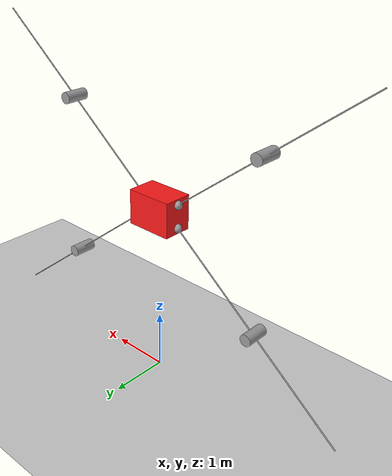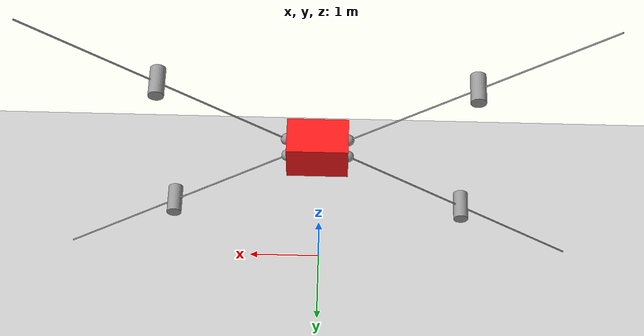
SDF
<?xml version="1.0" ?>
<sdf version="1.8">
    <world name="wallbot_world">
        <physics name="1ms" type="ode">
            <max_step_size>0.001</max_step_size>
            <real_time_factor>1.0</real_time_factor>
        </physics>
        <plugin
            filename="libignition-gazebo-physics-system.so"
            name="ignition::gazebo::systems::Physics">
        </plugin>
        <plugin
            filename="libignition-gazebo-user-commands-system.so"
            name="ignition::gazebo::systems::UserCommands">
        </plugin>
        <plugin
            filename="libignition-gazebo-scene-broadcaster-system.so"
            name="ignition::gazebo::systems::SceneBroadcaster">
        </plugin>
        <plugin
            filename="libignition-gazebo-sensors-system.so"
            name="ignition::gazebo::systems::Sensors">
            <render_engine>ogre2</render_engine>
        </plugin>
        <plugin
            filename="libignition-gazebo-contact-system.so"
            name="ignition::gazebo::systems::Contact">
        </plugin>

        <light type="directional" name="sun">
            <cast_shadows>true</cast_shadows>
            <pose>0 0 10 0 0 0</pose>
            <diffuse>0.8 0.8 0.8 1</diffuse>
            <specular>0.2 0.2 0.2 1</specular>
            <attenuation>
                <range>1000</range>
                <constant>0.9</constant>
                <linear>0.01</linear>
                <quadratic>0.001</quadratic>
            </attenuation>
            <direction>-0.5 0.1 -0.9</direction>
        </light>

        <model name="ground_plane">
            <static>true</static>
            <link name="link">
                <collision name="collision">
                <geometry>
                    <plane>
                    <normal>0 0 1</normal>
                    </plane>
                </geometry>
                </collision>
                <visual name="visual">
                <geometry>
                    <plane>
                    <normal>0 0 1</normal>
                    <size>100 100</size>
                    </plane>
                </geometry>
                <material>
                    <ambient>0.8 0.8 0.8 1</ambient>
                    <diffuse>0.8 0.8 0.8 1</diffuse>
                    <specular>0.8 0.8 0.8 1</specular>
                </material>
                </visual>
            </link>
        </model>

        <include>
          <uri>model://Wallbot_V3_Robot</uri>
          <name>wallbot</name>
          <pose>0 0 3 0 0 0</pose>
        </include>

        <include>
          <uri>model://BL_Anchor</uri>
          <name>bl_anchor</name>
          <pose>0 0 3 0 0 0</pose>
        </include>

        <include>
          <uri>model://BR_Anchor</uri>
          <name>br_anchor</name>
          <pose>0 0 3 0 0 0</pose>
        </include>

        <include>
          <uri>model://TL_Anchor</uri>
          <name>tl_anchor</name>
          <pose>0 0 3 0 0 0</pose>
        </include>

        <include>
          <uri>model://TR_Anchor</uri>
          <name>tr_anchor</name>
          <pose>0 0 3 0 0 0</pose>
        </include>

        <include>
          <uri>model://anchor_base</uri>
          <name>world_anchor</name>
          <pose>0 0 0 0 0 0</pose>
        </include>

    <joint name="bl_anchor_world_joint" type="fixed">
      <parent>world_anchor::world_anchor_link</parent>
      <child>bl_anchor::bl_link</child>
    </joint>

    <joint name="br_anchor_world_joint" type="fixed">
      <parent>world_anchor::world_anchor_link</parent>
      <child>br_anchor::br_link</child>
    </joint>

    <joint name="tl_anchor_world_joint" type="fixed">
      <parent>world_anchor::world_anchor_link</parent>
      <child>tl_anchor::tl_link</child>
    </joint>

    <joint name="tr_anchor_world_joint" type="fixed">
      <parent></parent>
      <child>tr_anchor::tr_link</child>
    </joint>

    </world>
</sdf>

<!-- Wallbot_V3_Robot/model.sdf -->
<sdf version='1.7'>
  <model name='Wallbot_V2_Robot'>
    <link name='link_0'>
      <inertial>
        <mass>1</mass>
        <inertia>
          <ixx>0.166667</ixx>
          <ixy>0</ixy>
          <ixz>0</ixz>
          <iyy>0.166667</iyy>
          <iyz>0</iyz>
          <izz>0.166667</izz>
        </inertia>
        <pose>0 0 0 0 -0 0</pose>
      </inertial>
      <pose>0.015 0 0.005 0 -0 0</pose>
      <self_collide>0</self_collide>
      <kinematic>0</kinematic>
      <enable_wind>0</enable_wind>
      <visual name='visual'>
        <pose>0 0 0 0 -0 0</pose>
        <geometry>
          <box>
            <size>0.8 0.5 0.6</size>
          </box>
        </geometry>
        <material>
          <lighting>1</lighting>
          <script>
            <uri>file://media/materials/scripts/gazebo.material</uri>
            <name>Gazebo/Grey</name>
          </script>
          <shader type='pixel'>
            <normal_map>__default__</normal_map>
          </shader>
          <ambient>1 0.1 0.1 1</ambient>
          <diffuse>0.7 0.7 0.7 1</diffuse>
          <specular>0.01 0.01 0.01 1</specular>
          <emissive>0 0 0 1</emissive>
        </material>
        <transparency>0</transparency>
        <cast_shadows>1</cast_shadows>
      </visual>
      <collision name='collision'>
        <laser_retro>0</laser_retro>
        <max_contacts>10</max_contacts>
        <pose>0 0 0 0 -0 0</pose>
        <geometry>
          <box>
            <size>0.8 0.5 0.6</size>
          </box>
        </geometry>
        <surface>
          <friction>
            <ode>
              <mu>0</mu>
              <mu2>0</mu2>
              <fdir1>0 0 0</fdir1>
              <slip1>0</slip1>
              <slip2>0</slip2>
            </ode>
            <torsional>
              <coefficient>0</coefficient>
              <patch_radius>0</patch_radius>
              <surface_radius>0</surface_radius>
              <use_patch_radius>0</use_patch_radius>
              <ode>
                <slip>0</slip>
              </ode>
            </torsional>
          </friction>
          <bounce>
            <restitution_coefficient>0</restitution_coefficient>
            <threshold>1e+06</threshold>
          </bounce>
          <contact>
            <collide_without_contact>0</collide_without_contact>
            <collide_without_contact_bitmask>1</collide_without_contact_bitmask>
            <collide_bitmask>1</collide_bitmask>
            <ode>
              <soft_cfm>0</soft_cfm>
              <soft_erp>0.2</soft_erp>
              <kp>1e+13</kp>
              <kd>1</kd>
              <max_vel>0.01</max_vel>
              <min_depth>0</min_depth>
            </ode>
            <bullet>
              <split_impulse>1</split_impulse>
              <split_impulse_penetration_threshold>-0.01</split_impulse_penetration_threshold>
              <soft_cfm>0</soft_cfm>
              <soft_erp>0.2</soft_erp>
              <kp>1e+13</kp>
              <kd>1</kd>
            </bullet>
          </contact>
        </surface>
      </collision>
    </link>
    <link name='link_0_0'>
      <inertial>
        <mass>1</mass>
        <inertia>
          <ixx>0.145833</ixx>
          <ixy>0</ixy>
          <ixz>0</ixz>
          <iyy>0.145833</iyy>
          <iyz>0</iyz>
          <izz>0.125</izz>
        </inertia>
        <pose>0 0 -2 0 -0 0</pose>
      </inertial>
      <pose>0.415 0 0.205 3.14159 -0.901593 3.14159</pose>

      <self_collide>0</self_collide>
      <kinematic>0</kinematic>
      <enable_wind>0</enable_wind>
      <visual name='visual'>
        <pose>0 0 -2 0 -0 0</pose>
        <geometry>
          <cylinder>
            <radius>0.01</radius>
            <length>4</length>
          </cylinder>
        </geometry>
        <material>
          <lighting>1</lighting>
          <script>
            <uri>file://media/materials/scripts/gazebo.material</uri>
            <name>Gazebo/Grey</name>
          </script>
          <shader type='pixel'>
            <normal_map>__default__</normal_map>
          </shader>
          <ambient>0.3 0.3 0.3 1</ambient>
          <diffuse>0.7 0.7 0.7 1</diffuse>
          <specular>0.01 0.01 0.01 1</specular>
          <emissive>0 0 0 1</emissive>
        </material>
        <transparency>0</transparency>
        <cast_shadows>1</cast_shadows>
      </visual>
      <collision name='collision'>
        <laser_retro>0</laser_retro>
        <max_contacts>10</max_contacts>
        <pose>0 0 -2 0 -0 0</pose>
        <geometry>
          <cylinder>
            <radius>0.01</radius>
            <length>4</length>
          </cylinder>
        </geometry>
        <surface>
          <friction>
            <ode>
              <mu>0</mu>
              <mu2>0</mu2>
              <fdir1>0 0 0</fdir1>
              <slip1>0</slip1>
              <slip2>0</slip2>
            </ode>
            <torsional>
              <coefficient>0</coefficient>
              <patch_radius>0</patch_radius>
              <surface_radius>0</surface_radius>
              <use_patch_radius>0</use_patch_radius>
              <ode>
                <slip>0</slip>
              </ode>
            </torsional>
          </friction>
          <bounce>
            <restitution_coefficient>0</restitution_coefficient>
            <threshold>1e+06</threshold>
          </bounce>
          <contact>
            <collide_without_contact>0</collide_without_contact>
            <collide_without_contact_bitmask>1</collide_without_contact_bitmask>
            <collide_bitmask>1</collide_bitmask>
            <ode>
              <soft_cfm>0</soft_cfm>
              <soft_erp>0.2</soft_erp>
              <kp>1e+13</kp>
              <kd>1</kd>
              <max_vel>0.01</max_vel>
              <min_depth>0</min_depth>
            </ode>
            <bullet>
              <split_impulse>1</split_impulse>
              <split_impulse_penetration_threshold>-0.01</split_impulse_penetration_threshold>
              <soft_cfm>0</soft_cfm>
              <soft_erp>0.2</soft_erp>
              <kp>1e+13</kp>
              <kd>1</kd>
            </bullet>
          </contact>
        </surface>
      </collision>
    </link>
    <link name='link_0_0_clone'>
      <inertial>
        <mass>1</mass>
        <inertia>
          <ixx>0.145833</ixx>
          <ixy>0</ixy>
          <ixz>0</ixz>
          <iyy>0.145833</iyy>
          <iyz>0</iyz>
          <izz>0.125</izz>
        </inertia>
        <pose>0 0 -2 0 -0 0</pose>
      </inertial>
      <pose>-0.385 0 0.205 -3.14159 0.9 -3.14159</pose>

      <self_collide>0</self_collide>
      <kinematic>0</kinematic>
      <enable_wind>0</enable_wind>
      <visual name='visual_0'>
        <pose>0 0 -2 0 -0 0</pose>
        <geometry>
          <cylinder>
            <radius>0.01</radius>
            <length>4</length>
          </cylinder>
        </geometry>
        <material>
          <lighting>1</lighting>
          <script>
            <uri>file://media/materials/scripts/gazebo.material</uri>
            <name>Gazebo/Grey</name>
          </script>
          <shader type='pixel'>
            <normal_map>__default__</normal_map>
          </shader>
          <ambient>0.3 0.3 0.3 1</ambient>
          <diffuse>0.7 0.7 0.7 1</diffuse>
          <specular>0.01 0.01 0.01 1</specular>
          <emissive>0 0 0 1</emissive>
        </material>
        <transparency>0</transparency>
        <cast_shadows>1</cast_shadows>
      </visual>
      <collision name='collision'>
        <laser_retro>0</laser_retro>
        <max_contacts>10</max_contacts>
        <pose>0 0 -2 0 -0 0</pose>
        <geometry>
          <cylinder>
            <radius>0.01</radius>
            <length>4</length>
          </cylinder>
        </geometry>
        <surface>
          <friction>
            <ode>
              <mu>0</mu>
              <mu2>0</mu2>
              <fdir1>0 0 0</fdir1>
              <slip1>0</slip1>
              <slip2>0</slip2>
            </ode>
            <torsional>
              <coefficient>0</coefficient>
              <patch_radius>0</patch_radius>
              <surface_radius>0</surface_radius>
              <use_patch_radius>0</use_patch_radius>
              <ode>
                <slip>0</slip>
              </ode>
            </torsional>
          </friction>
          <bounce>
            <restitution_coefficient>0</restitution_coefficient>
            <threshold>1e+06</threshold>
          </bounce>
          <contact>
            <collide_without_contact>0</collide_without_contact>
            <collide_without_contact_bitmask>1</collide_without_contact_bitmask>
            <collide_bitmask>1</collide_bitmask>
            <ode>
              <soft_cfm>0</soft_cfm>
              <soft_erp>0.2</soft_erp>
              <kp>1e+13</kp>
              <kd>1</kd>
              <max_vel>0.01</max_vel>
              <min_depth>0</min_depth>
            </ode>
            <bullet>
              <split_impulse>1</split_impulse>
              <split_impulse_penetration_threshold>-0.01</split_impulse_penetration_threshold>
              <soft_cfm>0</soft_cfm>
              <soft_erp>0.2</soft_erp>
              <kp>1e+13</kp>
              <kd>1</kd>
            </bullet>
          </contact>
        </surface>
      </collision>
    </link>
    <link name='link_0_0_clone_0'>
      <inertial>
        <mass>1</mass>
        <inertia>
          <ixx>0.145833</ixx>
          <ixy>0</ixy>
          <ixz>0</ixz>
          <iyy>0.145833</iyy>
          <iyz>0</iyz>
          <izz>0.125</izz>
        </inertia>
        <pose>0 0 -2 0 -0 0</pose>
      </inertial>
      <pose>0.415 0 -0.195 1.1e-05 -0.9 -5e-06</pose>

      <self_collide>0</self_collide>
      <kinematic>0</kinematic>
      <enable_wind>0</enable_wind>
      <visual name='visual_0'>
        <pose>0 0 -2 0 -0 0</pose>
        <geometry>
          <cylinder>
            <radius>0.01</radius>
            <length>4</length>
          </cylinder>
        </geometry>
        <material>
          <lighting>1</lighting>
          <script>
            <uri>file://media/materials/scripts/gazebo.material</uri>
            <name>Gazebo/Grey</name>
          </script>
          <shader type='pixel'>
            <normal_map>__default__</normal_map>
          </shader>
          <ambient>0.3 0.3 0.3 1</ambient>
          <diffuse>0.7 0.7 0.7 1</diffuse>
          <specular>0.01 0.01 0.01 1</specular>
          <emissive>0 0 0 1</emissive>
        </material>
        <transparency>0</transparency>
        <cast_shadows>1</cast_shadows>
      </visual>
      <collision name='collision'>
        <laser_retro>0</laser_retro>
        <max_contacts>10</max_contacts>
        <pose>0 0 -2 0 -0 0</pose>
        <geometry>
          <cylinder>
            <radius>0.01</radius>
            <length>4</length>
          </cylinder>
        </geometry>
        <surface>
          <friction>
            <ode>
              <mu>0</mu>
              <mu2>0</mu2>
              <fdir1>0 0 0</fdir1>
              <slip1>0</slip1>
              <slip2>0</slip2>
            </ode>
            <torsional>
              <coefficient>0</coefficient>
              <patch_radius>0</patch_radius>
              <surface_radius>0</surface_radius>
              <use_patch_radius>0</use_patch_radius>
              <ode>
                <slip>0</slip>
              </ode>
            </torsional>
          </friction>
          <bounce>
            <restitution_coefficient>0</restitution_coefficient>
            <threshold>1e+06</threshold>
          </bounce>
          <contact>
            <collide_without_contact>0</collide_without_contact>
            <collide_without_contact_bitmask>1</collide_without_contact_bitmask>
            <collide_bitmask>1</collide_bitmask>
            <ode>
              <soft_cfm>0</soft_cfm>
              <soft_erp>0.2</soft_erp>
              <kp>1e+13</kp>
              <kd>1</kd>
              <max_vel>0.01</max_vel>
              <min_depth>0</min_depth>
            </ode>
            <bullet>
              <split_impulse>1</split_impulse>
              <split_impulse_penetration_threshold>-0.01</split_impulse_penetration_threshold>
              <soft_cfm>0</soft_cfm>
              <soft_erp>0.2</soft_erp>
              <kp>1e+13</kp>
              <kd>1</kd>
            </bullet>
          </contact>
        </surface>
      </collision>
    </link>
    <link name='link_0_0_clone_1'>
      <inertial>
        <mass>1</mass>
        <inertia>
          <ixx>0.145833</ixx>
          <ixy>0</ixy>
          <ixz>0</ixz>
          <iyy>0.145833</iyy>
          <iyz>0</iyz>
          <izz>0.125</izz>
        </inertia>
        <pose>0 0 -2 0 -0 0</pose>
      </inertial>
      <pose>-0.385 0 -0.195 1.1e-05 0.9 -5e-06</pose>

      <self_collide>0</self_collide>
      <kinematic>0</kinematic>
      <enable_wind>0</enable_wind>
      <visual name='visual_0'>
        <pose>0 0 -2 0 -0 0</pose>
        <geometry>
          <cylinder>
            <radius>0.01</radius>
            <length>4</length>
          </cylinder>
        </geometry>
        <material>
          <lighting>1</lighting>
          <script>
            <uri>file://media/materials/scripts/gazebo.material</uri>
            <name>Gazebo/Grey</name>
          </script>
          <shader type='pixel'>
            <normal_map>__default__</normal_map>
          </shader>
          <ambient>0.3 0.3 0.3 1</ambient>
          <diffuse>0.7 0.7 0.7 1</diffuse>
          <specular>0.01 0.01 0.01 1</specular>
          <emissive>0 0 0 1</emissive>
        </material>
        <transparency>0</transparency>
        <cast_shadows>1</cast_shadows>
      </visual>
      <collision name='collision'>
        <laser_retro>0</laser_retro>
        <max_contacts>10</max_contacts>
        <pose>0 0 -2 0 -0 0</pose>
        <geometry>
          <cylinder>
            <radius>0.01</radius>
            <length>4</length>
          </cylinder>
        </geometry>
        <surface>
          <friction>
            <ode>
              <mu>0</mu>
              <mu2>0</mu2>
              <fdir1>0 0 0</fdir1>
              <slip1>0</slip1>
              <slip2>0</slip2>
            </ode>
            <torsional>
              <coefficient>0</coefficient>
              <patch_radius>0</patch_radius>
              <surface_radius>0</surface_radius>
              <use_patch_radius>0</use_patch_radius>
              <ode>
                <slip>0</slip>
              </ode>
            </torsional>
          </friction>
          <bounce>
            <restitution_coefficient>0</restitution_coefficient>
            <threshold>1e+06</threshold>
          </bounce>
          <contact>
            <collide_without_contact>0</collide_without_contact>
            <collide_without_contact_bitmask>1</collide_without_contact_bitmask>
            <collide_bitmask>1</collide_bitmask>
            <ode>
              <soft_cfm>0</soft_cfm>
              <soft_erp>0.2</soft_erp>
              <kp>1e+13</kp>
              <kd>1</kd>
              <max_vel>0.01</max_vel>
              <min_depth>0</min_depth>
            </ode>
            <bullet>
              <split_impulse>1</split_impulse>
              <split_impulse_penetration_threshold>-0.01</split_impulse_penetration_threshold>
              <soft_cfm>0</soft_cfm>
              <soft_erp>0.2</soft_erp>
              <kp>1e+13</kp>
              <kd>1</kd>
            </bullet>
          </contact>
        </surface>
      </collision>
    </link>
    <link name='link_1'>
      <inertial>
        <mass>1</mass>
        <inertia>
          <ixx>0.1</ixx>
          <ixy>0</ixy>
          <ixz>0</ixz>
          <iyy>0.1</iyy>
          <iyz>0</iyz>
          <izz>0.1</izz>
        </inertia>
        <pose>0 0 0 0 -0 0</pose>
      </inertial>
      <pose>-0.385 0 0.205 0 -0 0</pose>

      <self_collide>0</self_collide>
      <kinematic>0</kinematic>
      <enable_wind>0</enable_wind>
      <visual name='visual'>
        <pose>0 0 0 0 -0 0</pose>
        <geometry>
          <sphere>
            <radius>0.075</radius>
          </sphere>
        </geometry>
        <material>
          <lighting>1</lighting>
          <script>
            <uri>file://media/materials/scripts/gazebo.material</uri>
            <name>Gazebo/Grey</name>
          </script>
          <shader type='pixel'>
            <normal_map>__default__</normal_map>
          </shader>
          <ambient>0.3 0.3 0.3 1</ambient>
          <diffuse>0.7 0.7 0.7 1</diffuse>
          <specular>0.01 0.01 0.01 1</specular>
          <emissive>0 0 0 1</emissive>
        </material>
        <transparency>0</transparency>
        <cast_shadows>1</cast_shadows>
      </visual>
      <collision name='collision'>
        <laser_retro>0</laser_retro>
        <max_contacts>10</max_contacts>
        <pose>0 0 0 0 -0 0</pose>
        <geometry>
          <sphere>
            <radius>0.075</radius>
          </sphere>
        </geometry>
        <surface>
          <friction>
            <ode>
              <mu>0</mu>
              <mu2>0</mu2>
              <fdir1>0 0 0</fdir1>
              <slip1>0</slip1>
              <slip2>0</slip2>
            </ode>
            <torsional>
              <coefficient>0</coefficient>
              <patch_radius>0</patch_radius>
              <surface_radius>0</surface_radius>
              <use_patch_radius>0</use_patch_radius>
              <ode>
                <slip>0</slip>
              </ode>
            </torsional>
          </friction>
          <bounce>
            <restitution_coefficient>0</restitution_coefficient>
            <threshold>1e+06</threshold>
          </bounce>
          <contact>
            <collide_without_contact>0</collide_without_contact>
            <collide_without_contact_bitmask>1</collide_without_contact_bitmask>
            <collide_bitmask>1</collide_bitmask>
            <ode>
              <soft_cfm>0</soft_cfm>
              <soft_erp>0.2</soft_erp>
              <kp>1e+13</kp>
              <kd>1</kd>
              <max_vel>0.01</max_vel>
              <min_depth>0</min_depth>
            </ode>
            <bullet>
              <split_impulse>1</split_impulse>
              <split_impulse_penetration_threshold>-0.01</split_impulse_penetration_threshold>
              <soft_cfm>0</soft_cfm>
              <soft_erp>0.2</soft_erp>
              <kp>1e+13</kp>
              <kd>1</kd>
            </bullet>
          </contact>
        </surface>
      </collision>
    </link>
    <link name='link_1_0'>
      <inertial>
        <mass>1</mass>
        <inertia>
          <ixx>0.1</ixx>
          <ixy>0</ixy>
          <ixz>0</ixz>
          <iyy>0.1</iyy>
          <iyz>0</iyz>
          <izz>0.1</izz>
        </inertia>
        <pose>0 0 0 0 -0 0</pose>
      </inertial>
      <pose>-1.95165 1e-06 1.44822 0 -0 0</pose>

      <self_collide>0</self_collide>
      <kinematic>0</kinematic>
      <enable_wind>0</enable_wind>
      <visual name='visual'>
        <pose>0 0 0 0 -0 0</pose>
        <geometry>
          <sphere>
            <radius>0.01</radius>
          </sphere>
        </geometry>
        <material>
          <lighting>1</lighting>
          <script>
            <uri>file://media/materials/scripts/gazebo.material</uri>
            <name>Gazebo/Grey</name>
          </script>
          <shader type='pixel'>
            <normal_map>__default__</normal_map>
          </shader>
          <ambient>0.3 0.3 0.3 1</ambient>
          <diffuse>0.7 0.7 0.7 1</diffuse>
          <specular>0.01 0.01 0.01 1</specular>
          <emissive>0 0 0 1</emissive>
        </material>
        <transparency>0</transparency>
        <cast_shadows>1</cast_shadows>
      </visual>
      <collision name='collision'>
        <laser_retro>0</laser_retro>
        <max_contacts>10</max_contacts>
        <pose>0 0 0 0 -0 0</pose>
        <geometry>
          <sphere>
            <radius>0.01</radius>
          </sphere>
        </geometry>
        <surface>
          <friction>
            <ode>
              <mu>0</mu>
              <mu2>0</mu2>
              <fdir1>0 0 0</fdir1>
              <slip1>0</slip1>
              <slip2>0</slip2>
            </ode>
            <torsional>
              <coefficient>0</coefficient>
              <patch_radius>0</patch_radius>
              <surface_radius>0</surface_radius>
              <use_patch_radius>0</use_patch_radius>
              <ode>
                <slip>0</slip>
              </ode>
            </torsional>
          </friction>
          <bounce>
            <restitution_coefficient>0</restitution_coefficient>
            <threshold>1e+06</threshold>
          </bounce>
          <contact>
            <collide_without_contact>0</collide_without_contact>
            <collide_without_contact_bitmask>1</collide_without_contact_bitmask>
            <collide_bitmask>1</collide_bitmask>
            <ode>
              <soft_cfm>0</soft_cfm>
              <soft_erp>0.2</soft_erp>
              <kp>1e+13</kp>
              <kd>1</kd>
              <max_vel>0.01</max_vel>
              <min_depth>0</min_depth>
            </ode>
            <bullet>
              <split_impulse>1</split_impulse>
              <split_impulse_penetration_threshold>-0.01</split_impulse_penetration_threshold>
              <soft_cfm>0</soft_cfm>
              <soft_erp>0.2</soft_erp>
              <kp>1e+13</kp>
              <kd>1</kd>
            </bullet>
          </contact>
        </surface>
      </collision>
    </link>
    <link name='link_1_0_clone'>
      <inertial>
        <mass>1</mass>
        <inertia>
          <ixx>0.1</ixx>
          <ixy>0</ixy>
          <ixz>0</ixz>
          <iyy>0.1</iyy>
          <iyz>0</iyz>
          <izz>0.1</izz>
        </inertia>
        <pose>0 0 0 0 -0 0</pose>
      </inertial>
      <pose>1.98363 -1e-05 1.44572 0 -0 0</pose>

      <self_collide>0</self_collide>
      <kinematic>0</kinematic>
      <enable_wind>0</enable_wind>
      <visual name='visual'>
        <pose>0 0 0 0 -0 0</pose>
        <geometry>
          <sphere>
            <radius>0.01</radius>
          </sphere>
        </geometry>
        <material>
          <lighting>1</lighting>
          <script>
            <uri>file://media/materials/scripts/gazebo.material</uri>
            <name>Gazebo/Grey</name>
          </script>
          <shader type='pixel'>
            <normal_map>__default__</normal_map>
          </shader>
          <ambient>0.3 0.3 0.3 1</ambient>
          <diffuse>0.7 0.7 0.7 1</diffuse>
          <specular>0.01 0.01 0.01 1</specular>
          <emissive>0 0 0 1</emissive>
        </material>
        <transparency>0</transparency>
        <cast_shadows>1</cast_shadows>
      </visual>
      <collision name='collision'>
        <laser_retro>0</laser_retro>
        <max_contacts>10</max_contacts>
        <pose>0 0 0 0 -0 0</pose>
        <geometry>
          <sphere>
            <radius>0.01</radius>
          </sphere>
        </geometry>
        <surface>
          <friction>
            <ode>
              <mu>0</mu>
              <mu2>0</mu2>
              <fdir1>0 0 0</fdir1>
              <slip1>0</slip1>
              <slip2>0</slip2>
            </ode>
            <torsional>
              <coefficient>0</coefficient>
              <patch_radius>0</patch_radius>
              <surface_radius>0</surface_radius>
              <use_patch_radius>0</use_patch_radius>
              <ode>
                <slip>0</slip>
              </ode>
            </torsional>
          </friction>
          <bounce>
            <restitution_coefficient>0</restitution_coefficient>
            <threshold>1e+06</threshold>
          </bounce>
          <contact>
            <collide_without_contact>0</collide_without_contact>
            <collide_without_contact_bitmask>1</collide_without_contact_bitmask>
            <collide_bitmask>1</collide_bitmask>
            <ode>
              <soft_cfm>0</soft_cfm>
              <soft_erp>0.2</soft_erp>
              <kp>1e+13</kp>
              <kd>1</kd>
              <max_vel>0.01</max_vel>
              <min_depth>0</min_depth>
            </ode>
            <bullet>
              <split_impulse>1</split_impulse>
              <split_impulse_penetration_threshold>-0.01</split_impulse_penetration_threshold>
              <soft_cfm>0</soft_cfm>
              <soft_erp>0.2</soft_erp>
              <kp>1e+13</kp>
              <kd>1</kd>
            </bullet>
          </contact>
        </surface>
      </collision>
    </link>
    <link name='link_1_0_clone_0'>
      <inertial>
        <mass>1</mass>
        <inertia>
          <ixx>0.1</ixx>
          <ixy>0</ixy>
          <ixz>0</ixz>
          <iyy>0.1</iyy>
          <iyz>0</iyz>
          <izz>0.1</izz>
        </inertia>
        <pose>0 0 0 0 -0 0</pose>
      </inertial>
      <pose>1.98165 1.4e-05 -1.43822 1.1e-05 -0.9 -5e-06</pose>

      <self_collide>0</self_collide>
      <kinematic>0</kinematic>
      <enable_wind>0</enable_wind>
      <visual name='visual'>
        <pose>0 0 0 0 -0 0</pose>
        <geometry>
          <sphere>
            <radius>0.01</radius>
          </sphere>
        </geometry>
        <material>
          <lighting>1</lighting>
          <script>
            <uri>file://media/materials/scripts/gazebo.material</uri>
            <name>Gazebo/Grey</name>
          </script>
          <shader type='pixel'>
            <normal_map>__default__</normal_map>
          </shader>
          <ambient>0.3 0.3 0.3 1</ambient>
          <diffuse>0.7 0.7 0.7 1</diffuse>
          <specular>0.01 0.01 0.01 1</specular>
          <emissive>0 0 0 1</emissive>
        </material>
        <transparency>0</transparency>
        <cast_shadows>1</cast_shadows>
      </visual>
      <collision name='collision'>
        <laser_retro>0</laser_retro>
        <max_contacts>10</max_contacts>
        <pose>0 0 0 0 -0 0</pose>
        <geometry>
          <sphere>
            <radius>0.01</radius>
          </sphere>
        </geometry>
        <surface>
          <friction>
            <ode>
              <mu>0</mu>
              <mu2>0</mu2>
              <fdir1>0 0 0</fdir1>
              <slip1>0</slip1>
              <slip2>0</slip2>
            </ode>
            <torsional>
              <coefficient>0</coefficient>
              <patch_radius>0</patch_radius>
              <surface_radius>0</surface_radius>
              <use_patch_radius>0</use_patch_radius>
              <ode>
                <slip>0</slip>
              </ode>
            </torsional>
          </friction>
          <bounce>
            <restitution_coefficient>0</restitution_coefficient>
            <threshold>1e+06</threshold>
          </bounce>
          <contact>
            <collide_without_contact>0</collide_without_contact>
            <collide_without_contact_bitmask>1</collide_without_contact_bitmask>
            <collide_bitmask>1</collide_bitmask>
            <ode>
              <soft_cfm>0</soft_cfm>
              <soft_erp>0.2</soft_erp>
              <kp>1e+13</kp>
              <kd>1</kd>
              <max_vel>0.01</max_vel>
              <min_depth>0</min_depth>
            </ode>
            <bullet>
              <split_impulse>1</split_impulse>
              <split_impulse_penetration_threshold>-0.01</split_impulse_penetration_threshold>
              <soft_cfm>0</soft_cfm>
              <soft_erp>0.2</soft_erp>
              <kp>1e+13</kp>
              <kd>1</kd>
            </bullet>
          </contact>
        </surface>
      </collision>
    </link>
    <link name='link_1_0_clone_1'>
      <inertial>
        <mass>1</mass>
        <inertia>
          <ixx>0.1</ixx>
          <ixy>0</ixy>
          <ixz>0</ixz>
          <iyy>0.1</iyy>
          <iyz>0</iyz>
          <izz>0.1</izz>
        </inertia>
        <pose>0 0 0 0 -0 0</pose>
      </inertial>
      <pose>-1.95165 3e-05 -1.43822 1.1e-05 0.9 -5e-06</pose>

      <self_collide>0</self_collide>
      <kinematic>0</kinematic>
      <enable_wind>0</enable_wind>
      <visual name='visual'>
        <pose>0 0 0 0 -0 0</pose>
        <geometry>
          <sphere>
            <radius>0.01</radius>
          </sphere>
        </geometry>
        <material>
          <lighting>1</lighting>
          <script>
            <uri>file://media/materials/scripts/gazebo.material</uri>
            <name>Gazebo/Grey</name>
          </script>
          <shader type='pixel'>
            <normal_map>__default__</normal_map>
          </shader>
          <ambient>0.3 0.3 0.3 1</ambient>
          <diffuse>0.7 0.7 0.7 1</diffuse>
          <specular>0.01 0.01 0.01 1</specular>
          <emissive>0 0 0 1</emissive>
        </material>
        <transparency>0</transparency>
        <cast_shadows>1</cast_shadows>
      </visual>
      <collision name='collision'>
        <laser_retro>0</laser_retro>
        <max_contacts>10</max_contacts>
        <pose>0 0 0 0 -0 0</pose>
        <geometry>
          <sphere>
            <radius>0.01</radius>
          </sphere>
        </geometry>
        <surface>
          <friction>
            <ode>
              <mu>0</mu>
              <mu2>0</mu2>
              <fdir1>0 0 0</fdir1>
              <slip1>0</slip1>
              <slip2>0</slip2>
            </ode>
            <torsional>
              <coefficient>0</coefficient>
              <patch_radius>0</patch_radius>
              <surface_radius>0</surface_radius>
              <use_patch_radius>0</use_patch_radius>
              <ode>
                <slip>0</slip>
              </ode>
            </torsional>
          </friction>
          <bounce>
            <restitution_coefficient>0</restitution_coefficient>
            <threshold>1e+06</threshold>
          </bounce>
          <contact>
            <collide_without_contact>0</collide_without_contact>
            <collide_without_contact_bitmask>1</collide_without_contact_bitmask>
            <collide_bitmask>1</collide_bitmask>
            <ode>
              <soft_cfm>0</soft_cfm>
              <soft_erp>0.2</soft_erp>
              <kp>1e+13</kp>
              <kd>1</kd>
              <max_vel>0.01</max_vel>
              <min_depth>0</min_depth>
            </ode>
            <bullet>
              <split_impulse>1</split_impulse>
              <split_impulse_penetration_threshold>-0.01</split_impulse_penetration_threshold>
              <soft_cfm>0</soft_cfm>
              <soft_erp>0.2</soft_erp>
              <kp>1e+13</kp>
              <kd>1</kd>
            </bullet>
          </contact>
        </surface>
      </collision>
    </link>
    <link name='link_1_clone'>
      <inertial>
        <mass>1</mass>
        <inertia>
          <ixx>0.1</ixx>
          <ixy>0</ixy>
          <ixz>0</ixz>
          <iyy>0.1</iyy>
          <iyz>0</iyz>
          <izz>0.1</izz>
        </inertia>
        <pose>0 0 0 0 -0 0</pose>
      </inertial>
      <pose>0.415 0 0.205 0 -0 0</pose>

      <self_collide>0</self_collide>
      <kinematic>0</kinematic>
      <enable_wind>0</enable_wind>
      <visual name='visual'>
        <pose>0 0 0 0 -0 0</pose>
        <geometry>
          <sphere>
            <radius>0.075</radius>
          </sphere>
        </geometry>
        <material>
          <lighting>1</lighting>
          <script>
            <uri>file://media/materials/scripts/gazebo.material</uri>
            <name>Gazebo/Grey</name>
          </script>
          <shader type='pixel'>
            <normal_map>__default__</normal_map>
          </shader>
          <ambient>0.3 0.3 0.3 1</ambient>
          <diffuse>0.7 0.7 0.7 1</diffuse>
          <specular>0.01 0.01 0.01 1</specular>
          <emissive>0 0 0 1</emissive>
        </material>
        <transparency>0</transparency>
        <cast_shadows>1</cast_shadows>
      </visual>
      <collision name='collision'>
        <laser_retro>0</laser_retro>
        <max_contacts>10</max_contacts>
        <pose>0 0 0 0 -0 0</pose>
        <geometry>
          <sphere>
            <radius>0.075</radius>
          </sphere>
        </geometry>
        <surface>
          <friction>
            <ode>
              <mu>0</mu>
              <mu2>0</mu2>
              <fdir1>0 0 0</fdir1>
              <slip1>0</slip1>
              <slip2>0</slip2>
            </ode>
            <torsional>
              <coefficient>0</coefficient>
              <patch_radius>0</patch_radius>
              <surface_radius>0</surface_radius>
              <use_patch_radius>0</use_patch_radius>
              <ode>
                <slip>0</slip>
              </ode>
            </torsional>
          </friction>
          <bounce>
            <restitution_coefficient>0</restitution_coefficient>
            <threshold>1e+06</threshold>
          </bounce>
          <contact>
            <collide_without_contact>0</collide_without_contact>
            <collide_without_contact_bitmask>1</collide_without_contact_bitmask>
            <collide_bitmask>1</collide_bitmask>
            <ode>
              <soft_cfm>0</soft_cfm>
              <soft_erp>0.2</soft_erp>
              <kp>1e+13</kp>
              <kd>1</kd>
              <max_vel>0.01</max_vel>
              <min_depth>0</min_depth>
            </ode>
            <bullet>
              <split_impulse>1</split_impulse>
              <split_impulse_penetration_threshold>-0.01</split_impulse_penetration_threshold>
              <soft_cfm>0</soft_cfm>
              <soft_erp>0.2</soft_erp>
              <kp>1e+13</kp>
              <kd>1</kd>
            </bullet>
          </contact>
        </surface>
      </collision>
    </link>
    <link name='link_1_clone_0'>
      <inertial>
        <mass>1</mass>
        <inertia>
          <ixx>0.1</ixx>
          <ixy>0</ixy>
          <ixz>0</ixz>
          <iyy>0.1</iyy>
          <iyz>0</iyz>
          <izz>0.1</izz>
        </inertia>
        <pose>0 0 0 0 -0 0</pose>
      </inertial>
      <pose>0.415 0 -0.195 0 -0 0</pose>

      <self_collide>0</self_collide>
      <kinematic>0</kinematic>
      <enable_wind>0</enable_wind>
      <visual name='visual'>
        <pose>0 0 0 0 -0 0</pose>
        <geometry>
          <sphere>
            <radius>0.075</radius>
          </sphere>
        </geometry>
        <material>
          <lighting>1</lighting>
          <script>
            <uri>file://media/materials/scripts/gazebo.material</uri>
            <name>Gazebo/Grey</name>
          </script>
          <shader type='pixel'>
            <normal_map>__default__</normal_map>
          </shader>
          <ambient>0.3 0.3 0.3 1</ambient>
          <diffuse>0.7 0.7 0.7 1</diffuse>
          <specular>0.01 0.01 0.01 1</specular>
          <emissive>0 0 0 1</emissive>
        </material>
        <transparency>0</transparency>
        <cast_shadows>1</cast_shadows>
      </visual>
      <collision name='collision'>
        <laser_retro>0</laser_retro>
        <max_contacts>10</max_contacts>
        <pose>0 0 0 0 -0 0</pose>
        <geometry>
          <sphere>
            <radius>0.075</radius>
          </sphere>
        </geometry>
        <surface>
          <friction>
            <ode>
              <mu>0</mu>
              <mu2>0</mu2>
              <fdir1>0 0 0</fdir1>
              <slip1>0</slip1>
              <slip2>0</slip2>
            </ode>
            <torsional>
              <coefficient>0</coefficient>
              <patch_radius>0</patch_radius>
              <surface_radius>0</surface_radius>
              <use_patch_radius>0</use_patch_radius>
              <ode>
                <slip>0</slip>
              </ode>
            </torsional>
          </friction>
          <bounce>
            <restitution_coefficient>0</restitution_coefficient>
            <threshold>1e+06</threshold>
          </bounce>
          <contact>
            <collide_without_contact>0</collide_without_contact>
            <collide_without_contact_bitmask>1</collide_without_contact_bitmask>
            <collide_bitmask>1</collide_bitmask>
            <ode>
              <soft_cfm>0</soft_cfm>
              <soft_erp>0.2</soft_erp>
              <kp>1e+13</kp>
              <kd>1</kd>
              <max_vel>0.01</max_vel>
              <min_depth>0</min_depth>
            </ode>
            <bullet>
              <split_impulse>1</split_impulse>
              <split_impulse_penetration_threshold>-0.01</split_impulse_penetration_threshold>
              <soft_cfm>0</soft_cfm>
              <soft_erp>0.2</soft_erp>
              <kp>1e+13</kp>
              <kd>1</kd>
            </bullet>
          </contact>
        </surface>
      </collision>
    </link>
    <link name='link_1_clone_1'>
      <inertial>
        <mass>1</mass>
        <inertia>
          <ixx>0.1</ixx>
          <ixy>0</ixy>
          <ixz>0</ixz>
          <iyy>0.1</iyy>
          <iyz>0</iyz>
          <izz>0.1</izz>
        </inertia>
        <pose>0 0 0 0 -0 0</pose>
      </inertial>
      <pose>-0.385 0 -0.195 0 -0 0</pose>

      <self_collide>0</self_collide>
      <kinematic>0</kinematic>
      <enable_wind>0</enable_wind>
      <visual name='visual'>
        <pose>0 0 0 0 -0 0</pose>
        <geometry>
          <sphere>
            <radius>0.075</radius>
          </sphere>
        </geometry>
        <material>
          <lighting>1</lighting>
          <script>
            <uri>file://media/materials/scripts/gazebo.material</uri>
            <name>Gazebo/Grey</name>
          </script>
          <shader type='pixel'>
            <normal_map>__default__</normal_map>
          </shader>
          <ambient>0.3 0.3 0.3 1</ambient>
          <diffuse>0.7 0.7 0.7 1</diffuse>
          <specular>0.01 0.01 0.01 1</specular>
          <emissive>0 0 0 1</emissive>
        </material>
        <transparency>0</transparency>
        <cast_shadows>1</cast_shadows>
      </visual>
      <collision name='collision'>
        <laser_retro>0</laser_retro>
        <max_contacts>10</max_contacts>
        <pose>0 0 0 0 -0 0</pose>
        <geometry>
          <sphere>
            <radius>0.075</radius>
          </sphere>
        </geometry>
        <surface>
          <friction>
            <ode>
              <mu>0</mu>
              <mu2>0</mu2>
              <fdir1>0 0 0</fdir1>
              <slip1>0</slip1>
              <slip2>0</slip2>
            </ode>
            <torsional>
              <coefficient>0</coefficient>
              <patch_radius>0</patch_radius>
              <surface_radius>0</surface_radius>
              <use_patch_radius>0</use_patch_radius>
              <ode>
                <slip>0</slip>
              </ode>
            </torsional>
          </friction>
          <bounce>
            <restitution_coefficient>0</restitution_coefficient>
            <threshold>1e+06</threshold>
          </bounce>
          <contact>
            <collide_without_contact>0</collide_without_contact>
            <collide_without_contact_bitmask>1</collide_without_contact_bitmask>
            <collide_bitmask>1</collide_bitmask>
            <ode>
              <soft_cfm>0</soft_cfm>
              <soft_erp>0.2</soft_erp>
              <kp>1e+13</kp>
              <kd>1</kd>
              <max_vel>0.01</max_vel>
              <min_depth>0</min_depth>
            </ode>
            <bullet>
              <split_impulse>1</split_impulse>
              <split_impulse_penetration_threshold>-0.01</split_impulse_penetration_threshold>
              <soft_cfm>0</soft_cfm>
              <soft_erp>0.2</soft_erp>
              <kp>1e+13</kp>
              <kd>1</kd>
            </bullet>
          </contact>
        </surface>
      </collision>
    </link>
    <link name='link_3'>
      <inertial>
        <mass>1</mass>
        <inertia>
          <ixx>0.145833</ixx>
          <ixy>0</ixy>
          <ixz>0</ixz>
          <iyy>0.145833</iyy>
          <iyz>0</iyz>
          <izz>0.125</izz>
        </inertia>
        <pose>0 0 0 0 -0 0</pose>
      </inertial>
      <pose>-1.95165 1e-06 1.44822 0 -0 0</pose>

      <self_collide>0</self_collide>
      <kinematic>1</kinematic>
      <enable_wind>0</enable_wind>
      <visual name='visual'>
        <pose>0 0 0 1.57 -0 0</pose>
        <geometry>
          <cylinder>
            <radius>0.1</radius>
            <length>0.4</length>
          </cylinder>
        </geometry>
        <material>
          <lighting>1</lighting>
          <script>
            <uri>file://media/materials/scripts/gazebo.material</uri>
            <name>Gazebo/Grey</name>
          </script>
          <shader type='pixel'>
            <normal_map>__default__</normal_map>
          </shader>
          <ambient>0.3 0.3 0.3 1</ambient>
          <diffuse>0.7 0.7 0.7 1</diffuse>
          <specular>0.01 0.01 0.01 1</specular>
          <emissive>0 0 0 1</emissive>
        </material>
        <transparency>0</transparency>
        <cast_shadows>1</cast_shadows>
      </visual>
      <collision name='collision'>
        <laser_retro>0</laser_retro>
        <max_contacts>10</max_contacts>
        <pose>0 0 0 1.57 -0 0</pose>
        <geometry>
          <cylinder>
            <radius>0.1</radius>
            <length>0.4</length>
          </cylinder>
        </geometry>
        <surface>
          <friction>
            <ode>
              <mu>0</mu>
              <mu2>0</mu2>
              <fdir1>0 0 0</fdir1>
              <slip1>0</slip1>
              <slip2>0</slip2>
            </ode>
            <torsional>
              <coefficient>0</coefficient>
              <patch_radius>0</patch_radius>
              <surface_radius>0</surface_radius>
              <use_patch_radius>0</use_patch_radius>
              <ode>
                <slip>0</slip>
              </ode>
            </torsional>
          </friction>
          <bounce>
            <restitution_coefficient>0</restitution_coefficient>
            <threshold>1e+06</threshold>
          </bounce>
          <contact>
            <collide_without_contact>0</collide_without_contact>
            <collide_without_contact_bitmask>1</collide_without_contact_bitmask>
            <collide_bitmask>1</collide_bitmask>
            <ode>
              <soft_cfm>0</soft_cfm>
              <soft_erp>0.2</soft_erp>
              <kp>1e+13</kp>
              <kd>1</kd>
              <max_vel>0.01</max_vel>
              <min_depth>0</min_depth>
            </ode>
            <bullet>
              <split_impulse>1</split_impulse>
              <split_impulse_penetration_threshold>-0.01</split_impulse_penetration_threshold>
              <soft_cfm>0</soft_cfm>
              <soft_erp>0.2</soft_erp>
              <kp>1e+13</kp>
              <kd>1</kd>
            </bullet>
          </contact>
        </surface>
      </collision>
    </link>
    <link name='link_3_clone'>
      <inertial>
        <mass>1</mass>
        <inertia>
          <ixx>0.145833</ixx>
          <ixy>0</ixy>
          <ixz>0</ixz>
          <iyy>0.145833</iyy>
          <iyz>0</iyz>
          <izz>0.125</izz>
        </inertia>
        <pose>0 0 0 0 -0 0</pose>
      </inertial>
      <pose>1.98363 -1e-05 1.44572 0 -0 0</pose>

      <self_collide>0</self_collide>
      <kinematic>1</kinematic>
      <enable_wind>0</enable_wind>
      <visual name='visual'>
        <pose>0 0 0 1.57 -0 0</pose>
        <geometry>
          <cylinder>
            <radius>0.1</radius>
            <length>0.4</length>
          </cylinder>
        </geometry>
        <material>
          <lighting>1</lighting>
          <script>
            <uri>file://media/materials/scripts/gazebo.material</uri>
            <name>Gazebo/Grey</name>
          </script>
          <shader type='pixel'>
            <normal_map>__default__</normal_map>
          </shader>
          <ambient>0.3 0.3 0.3 1</ambient>
          <diffuse>0.7 0.7 0.7 1</diffuse>
          <specular>0.01 0.01 0.01 1</specular>
          <emissive>0 0 0 1</emissive>
        </material>
        <transparency>0</transparency>
        <cast_shadows>1</cast_shadows>
      </visual>
      <collision name='collision'>
        <laser_retro>0</laser_retro>
        <max_contacts>10</max_contacts>
        <pose>0 0 0 1.57 -0 0</pose>
        <geometry>
          <cylinder>
            <radius>0.1</radius>
            <length>0.4</length>
          </cylinder>
        </geometry>
        <surface>
          <friction>
            <ode>
              <mu>0</mu>
              <mu2>0</mu2>
              <fdir1>0 0 0</fdir1>
              <slip1>0</slip1>
              <slip2>0</slip2>
            </ode>
            <torsional>
              <coefficient>0</coefficient>
              <patch_radius>0</patch_radius>
              <surface_radius>0</surface_radius>
              <use_patch_radius>0</use_patch_radius>
              <ode>
                <slip>0</slip>
              </ode>
            </torsional>
          </friction>
          <bounce>
            <restitution_coefficient>0</restitution_coefficient>
            <threshold>1e+06</threshold>
          </bounce>
          <contact>
            <collide_without_contact>0</collide_without_contact>
            <collide_without_contact_bitmask>1</collide_without_contact_bitmask>
            <collide_bitmask>1</collide_bitmask>
            <ode>
              <soft_cfm>0</soft_cfm>
              <soft_erp>0.2</soft_erp>
              <kp>1e+13</kp>
              <kd>1</kd>
              <max_vel>0.01</max_vel>
              <min_depth>0</min_depth>
            </ode>
            <bullet>
              <split_impulse>1</split_impulse>
              <split_impulse_penetration_threshold>-0.01</split_impulse_penetration_threshold>
              <soft_cfm>0</soft_cfm>
              <soft_erp>0.2</soft_erp>
              <kp>1e+13</kp>
              <kd>1</kd>
            </bullet>
          </contact>
        </surface>
      </collision>
    </link>
    <link name='link_3_clone_0'>
      <inertial>
        <mass>1</mass>
        <inertia>
          <ixx>0.145833</ixx>
          <ixy>0</ixy>
          <ixz>0</ixz>
          <iyy>0.145833</iyy>
          <iyz>0</iyz>
          <izz>0.125</izz>
        </inertia>
        <pose>0 0 0 0 -0 0</pose>
      </inertial>
      <pose>1.98165 1.4e-05 -1.43822 1.1e-05 -0.9 -5e-06</pose>

      <self_collide>0</self_collide>
      <kinematic>1</kinematic>
      <enable_wind>0</enable_wind>
      <visual name='visual'>
        <pose>0 0 0 1.57 -0 0</pose>
        <geometry>
          <cylinder>
            <radius>0.1</radius>
            <length>0.4</length>
          </cylinder>
        </geometry>
        <material>
          <lighting>1</lighting>
          <script>
            <uri>file://media/materials/scripts/gazebo.material</uri>
            <name>Gazebo/Grey</name>
          </script>
          <shader type='pixel'>
            <normal_map>__default__</normal_map>
          </shader>
          <ambient>0.3 0.3 0.3 1</ambient>
          <diffuse>0.7 0.7 0.7 1</diffuse>
          <specular>0.01 0.01 0.01 1</specular>
          <emissive>0 0 0 1</emissive>
        </material>
        <transparency>0</transparency>
        <cast_shadows>1</cast_shadows>
      </visual>
      <collision name='collision'>
        <laser_retro>0</laser_retro>
        <max_contacts>10</max_contacts>
        <pose>0 0 0 1.57 -0 0</pose>
        <geometry>
          <cylinder>
            <radius>0.1</radius>
            <length>0.4</length>
          </cylinder>
        </geometry>
        <surface>
          <friction>
            <ode>
              <mu>0</mu>
              <mu2>0</mu2>
              <fdir1>0 0 0</fdir1>
              <slip1>0</slip1>
              <slip2>0</slip2>
            </ode>
            <torsional>
              <coefficient>0</coefficient>
              <patch_radius>0</patch_radius>
              <surface_radius>0</surface_radius>
              <use_patch_radius>0</use_patch_radius>
              <ode>
                <slip>0</slip>
              </ode>
            </torsional>
          </friction>
          <bounce>
            <restitution_coefficient>0</restitution_coefficient>
            <threshold>1e+06</threshold>
          </bounce>
          <contact>
            <collide_without_contact>0</collide_without_contact>
            <collide_without_contact_bitmask>1</collide_without_contact_bitmask>
            <collide_bitmask>1</collide_bitmask>
            <ode>
              <soft_cfm>0</soft_cfm>
              <soft_erp>0.2</soft_erp>
              <kp>1e+13</kp>
              <kd>1</kd>
              <max_vel>0.01</max_vel>
              <min_depth>0</min_depth>
            </ode>
            <bullet>
              <split_impulse>1</split_impulse>
              <split_impulse_penetration_threshold>-0.01</split_impulse_penetration_threshold>
              <soft_cfm>0</soft_cfm>
              <soft_erp>0.2</soft_erp>
              <kp>1e+13</kp>
              <kd>1</kd>
            </bullet>
          </contact>
        </surface>
      </collision>
    </link>
    <link name='link_3_clone_1'>
      <inertial>
        <mass>1</mass>
        <inertia>
          <ixx>0.145833</ixx>
          <ixy>0</ixy>
          <ixz>0</ixz>
          <iyy>0.145833</iyy>
          <iyz>0</iyz>
          <izz>0.125</izz>
        </inertia>
        <pose>0 0 0 0 -0 0</pose>
      </inertial>
      <pose>-1.95165 3e-05 -1.43822 1.1e-05 0.9 -5e-06</pose>

      <self_collide>0</self_collide>
      <enable_wind>0</enable_wind>
      <visual name='visual'>
        <pose>0 0 0 1.57 -0 0</pose>
        <geometry>
          <cylinder>
            <radius>0.1</radius>
            <length>0.4</length>
          </cylinder>
        </geometry>
        <material>
          <lighting>1</lighting>
          <script>
            <uri>file://media/materials/scripts/gazebo.material</uri>
            <name>Gazebo/Grey</name>
          </script>
          <shader type='pixel'>
            <normal_map>__default__</normal_map>
          </shader>
          <ambient>0.3 0.3 0.3 1</ambient>
          <diffuse>0.7 0.7 0.7 1</diffuse>
          <specular>0.01 0.01 0.01 1</specular>
          <emissive>0 0 0 1</emissive>
        </material>
        <transparency>0</transparency>
        <cast_shadows>1</cast_shadows>
      </visual>
      <collision name='collision'>
        <laser_retro>0</laser_retro>
        <max_contacts>10</max_contacts>
        <pose>0 0 0 1.57 -0 0</pose>
        <geometry>
          <cylinder>
            <radius>0.1</radius>
            <length>0.4</length>
          </cylinder>
        </geometry>
        <surface>
          <friction>
            <ode>
              <mu>0</mu>
              <mu2>0</mu2>
              <fdir1>0 0 0</fdir1>
              <slip1>0</slip1>
              <slip2>0</slip2>
            </ode>
            <torsional>
              <coefficient>0</coefficient>
              <patch_radius>0</patch_radius>
              <surface_radius>0</surface_radius>
              <use_patch_radius>0</use_patch_radius>
              <ode>
                <slip>0</slip>
              </ode>
            </torsional>
          </friction>
          <bounce>
            <restitution_coefficient>0</restitution_coefficient>
            <threshold>1e+06</threshold>
          </bounce>
          <contact>
            <collide_without_contact>0</collide_without_contact>
            <collide_without_contact_bitmask>1</collide_without_contact_bitmask>
            <collide_bitmask>1</collide_bitmask>
            <ode>
              <soft_cfm>0</soft_cfm>
              <soft_erp>0.2</soft_erp>
              <kp>1e+13</kp>
              <kd>1</kd>
              <max_vel>0.01</max_vel>
              <min_depth>0</min_depth>
            </ode>
            <bullet>
              <split_impulse>1</split_impulse>
              <split_impulse_penetration_threshold>-0.01</split_impulse_penetration_threshold>
              <soft_cfm>0</soft_cfm>
              <soft_erp>0.2</soft_erp>
              <kp>1e+13</kp>
              <kd>1</kd>
            </bullet>
          </contact>
        </surface>
      </collision>
    </link>
    <joint name='Prismatic Joint Bottom Left' type='prismatic'>
      <child>link_1_0_clone_0</child>
      <parent>link_0_0_clone_0</parent>
      <pose>0 0 0 0 -0 0</pose>
      <axis>
        <xyz>0 0 1</xyz>
        <limit>
          <lower>-2</lower>
          <upper>2</upper>
          <effort>-1</effort>
          <velocity>-1</velocity>
        </limit>
        <dynamics>
          <spring_reference>0</spring_reference>
          <spring_stiffness>0</spring_stiffness>
          <damping>0</damping>
          <friction>0</friction>
        </dynamics>
      </axis>
      <physics>
        <ode>
          <limit>
            <cfm>0</cfm>
            <erp>0.2</erp>
          </limit>
          <suspension>
            <cfm>0</cfm>
            <erp>0.2</erp>
          </suspension>
        </ode>
      </physics>
    </joint>
    <joint name='Prismatic Joint Bottom Right' type='prismatic'>
      <child>link_1_0_clone_1</child>
      <parent>link_0_0_clone_1</parent>
      <pose>0 0 0 0 -0 0</pose>
      <axis>
        <xyz>0 0 1</xyz>
        <limit>
          <lower>-2</lower>
          <upper>2</upper>
          <effort>-1</effort>
          <velocity>-1</velocity>
        </limit>
        <dynamics>
          <spring_reference>0</spring_reference>
          <spring_stiffness>0</spring_stiffness>
          <damping>0</damping>
          <friction>0</friction>
        </dynamics>
      </axis>
      <physics>
        <ode>
          <limit>
            <cfm>0</cfm>
            <erp>0.2</erp>
          </limit>
          <suspension>
            <cfm>0</cfm>
            <erp>0.2</erp>
          </suspension>
        </ode>
      </physics>
    </joint>
    <joint name='Prismatic Joint Top Left' type='prismatic'>
      <child>link_1_0_clone</child>
      <parent>link_0_0</parent>
      <pose>0 0 0 0 -0 0</pose>
      <axis>
        <xyz>0 0 1</xyz>
        <limit>
          <lower>-2</lower>
          <upper>2</upper>
          <effort>-1</effort>
          <velocity>-1</velocity>
        </limit>
        <dynamics>
          <spring_reference>0</spring_reference>
          <spring_stiffness>0</spring_stiffness>
          <damping>0</damping>
          <friction>0</friction>
        </dynamics>
      </axis>
      <physics>
        <ode>
          <limit>
            <cfm>0</cfm>
            <erp>0.2</erp>
          </limit>
          <suspension>
            <cfm>0</cfm>
            <erp>0.2</erp>
          </suspension>
        </ode>
      </physics>
    </joint>
    <joint name='Prismatic Joint Top Right' type='prismatic'>
      <child>link_1_0</child>
      <parent>link_0_0_clone</parent>
      <pose>0 0 0 0 -0 0</pose>
      <axis>
        <xyz>0 0 -1</xyz>
        <limit>
          <lower>-2</lower>
          <upper>2</upper>
          <effort>-1</effort>
          <velocity>-1</velocity>
        </limit>
        <dynamics>
          <spring_reference>0</spring_reference>
          <spring_stiffness>0</spring_stiffness>
          <damping>0</damping>
          <friction>0</friction>
        </dynamics>
      </axis>
      <physics>
        <ode>
          <limit>
            <cfm>0</cfm>
            <erp>0.2</erp>
          </limit>
          <suspension>
            <cfm>0</cfm>
            <erp>0.2</erp>
          </suspension>
        </ode>
      </physics>
    </joint>
    <joint name='Universal Join Bottom Left' type='universal'>
      <child>link_3_clone_0</child>
      <parent>link_1_0_clone_0</parent>
      <pose>0 0 0 0 -0 0</pose>
      <axis>
        <xyz>0 0 1</xyz>
        <limit>
          <lower>-1</lower>
          <upper>1</upper>
          <effort>-1</effort>
          <velocity>-1</velocity>
        </limit>
        <dynamics>
          <spring_reference>0</spring_reference>
          <spring_stiffness>0</spring_stiffness>
          <damping>0</damping>
          <friction>0</friction>
        </dynamics>
      </axis>
      <axis2>
        <xyz>0 1 0</xyz>
        <limit>
          <lower>-1</lower>
          <upper>1</upper>
          <effort>-1</effort>
          <velocity>-1</velocity>
        </limit>
        <dynamics>
          <spring_reference>0</spring_reference>
          <spring_stiffness>0</spring_stiffness>
          <damping>0</damping>
          <friction>0</friction>
        </dynamics>
      </axis2>
      <physics>
        <ode>
          <limit>
            <cfm>0</cfm>
            <erp>0.2</erp>
          </limit>
          <suspension>
            <cfm>0</cfm>
            <erp>0.2</erp>
          </suspension>
        </ode>
      </physics>
    </joint>
    <joint name='Universal Joint Bottom Right' type='universal'>
      <child>link_3_clone_1</child>
      <parent>link_1_0_clone_1</parent>
      <pose>0 0 0 0 -0 0</pose>
      <axis>
        <xyz>0 1 0</xyz>
        <limit>
          <lower>-1</lower>
          <upper>1</upper>
          <effort>-1</effort>
          <velocity>-1</velocity>
        </limit>
        <dynamics>
          <spring_reference>0</spring_reference>
          <spring_stiffness>0</spring_stiffness>
          <damping>0</damping>
          <friction>0</friction>
        </dynamics>
      </axis>
      <axis2>
        <xyz>0 0 1</xyz>
        <limit>
          <lower>-1</lower>
          <upper>1</upper>
          <effort>-1</effort>
          <velocity>-1</velocity>
        </limit>
        <dynamics>
          <spring_reference>0</spring_reference>
          <spring_stiffness>0</spring_stiffness>
          <damping>0</damping>
          <friction>0</friction>
        </dynamics>
      </axis2>
      <physics>
        <ode>
          <limit>
            <cfm>0</cfm>
            <erp>0.2</erp>
          </limit>
          <suspension>
            <cfm>0</cfm>
            <erp>0.2</erp>
          </suspension>
        </ode>
      </physics>
    </joint>
    <joint name='Universal Joint Top Left' type='universal'>
      <child>link_3_clone</child>
      <parent>link_1_0_clone</parent>
      <pose>0 0 0 0 -0 0</pose>
      <axis>
        <xyz>1 0 0</xyz>
        <limit>
          <lower>-1</lower>
          <upper>1</upper>
          <effort>-1</effort>
          <velocity>-1</velocity>
        </limit>
        <dynamics>
          <spring_reference>0</spring_reference>
          <spring_stiffness>0</spring_stiffness>
          <damping>0</damping>
          <friction>0</friction>
        </dynamics>
      </axis>
      <axis2>
        <xyz>0 0 1</xyz>
        <limit>
          <lower>-1e+16</lower>
          <upper>1e+16</upper>
          <effort>-1</effort>
          <velocity>-1</velocity>
        </limit>
        <dynamics>
          <spring_reference>0</spring_reference>
          <spring_stiffness>0</spring_stiffness>
          <damping>0</damping>
          <friction>0</friction>
        </dynamics>
      </axis2>
      <physics>
        <ode>
          <limit>
            <cfm>0</cfm>
            <erp>0.2</erp>
          </limit>
          <suspension>
            <cfm>0</cfm>
            <erp>0.2</erp>
          </suspension>
        </ode>
      </physics>
    </joint>
    <joint name='Universal Joint Top Right' type='universal'>
      <child>link_3</child>
      <parent>link_1_0</parent>
      <pose>0 0 0 0 -0 0</pose>
      <axis>
        <xyz>0 1 0</xyz>
        <limit>
          <lower>-1</lower>
          <upper>1</upper>
          <effort>-1</effort>
          <velocity>-1</velocity>
        </limit>
        <dynamics>
          <spring_reference>0</spring_reference>
          <spring_stiffness>0</spring_stiffness>
          <damping>0</damping>
          <friction>0</friction>
        </dynamics>
      </axis>
      <axis2>
        <xyz>0 0 1</xyz>
        <limit>
          <lower>-1</lower>
          <upper>1</upper>
          <effort>-1</effort>
          <velocity>-1</velocity>
        </limit>
        <dynamics>
          <spring_reference>0</spring_reference>
          <spring_stiffness>0</spring_stiffness>
          <damping>0</damping>
          <friction>0</friction>
        </dynamics>
      </axis2>
      <physics>
        <ode>
          <limit>
            <cfm>0</cfm>
            <erp>0.2</erp>
          </limit>
          <suspension>
            <cfm>0</cfm>
            <erp>0.2</erp>
          </suspension>
        </ode>
      </physics>
    </joint>
    <joint name='link_0_JOINT_0' type='fixed'>
      <parent>link_0</parent>
      <child>link_1</child>
      <pose>0 0 0 0 -0 0</pose>
      <physics>
        <ode>
          <limit>
            <cfm>0</cfm>
            <erp>0.2</erp>
          </limit>
          <suspension>
            <cfm>0</cfm>
            <erp>0.2</erp>
          </suspension>
        </ode>
      </physics>
    </joint>
    <joint name='link_0_JOINT_1' type='fixed'>
      <parent>link_0</parent>
      <child>link_1_clone_1</child>
      <pose>0 0 0 0 -0 0</pose>
      <physics>
        <ode>
          <limit>
            <cfm>0</cfm>
            <erp>0.2</erp>
          </limit>
          <suspension>
            <cfm>0</cfm>
            <erp>0.2</erp>
          </suspension>
        </ode>
      </physics>
    </joint>
    <joint name='link_0_JOINT_2' type='fixed'>
      <parent>link_0</parent>
      <child>link_1_clone</child>
      <pose>0 0 0 0 -0 0</pose>
      <physics>
        <ode>
          <limit>
            <cfm>0</cfm>
            <erp>0.2</erp>
          </limit>
          <suspension>
            <cfm>0</cfm>
            <erp>0.2</erp>
          </suspension>
        </ode>
      </physics>
    </joint>
    <joint name='link_0_JOINT_3' type='fixed'>
      <parent>link_0</parent>
      <child>link_1_clone_0</child>
      <pose>0 0 0 0 -0 0</pose>
      <physics>
        <ode>
          <limit>
            <cfm>0</cfm>
            <erp>0.2</erp>
          </limit>
          <suspension>
            <cfm>0</cfm>
            <erp>0.2</erp>
          </suspension>
        </ode>
      </physics>
    </joint>
    <joint name='link_1_JOINT_2' type='ball'>
      <parent>link_1</parent>
      <child>link_0_0_clone</child>
      <pose>0 0 0 0 -0 0</pose>
      <physics>
        <ode>
          <limit>
            <cfm>0</cfm>
            <erp>0.2</erp>
          </limit>
          <suspension>
            <cfm>0</cfm>
            <erp>0.2</erp>
          </suspension>
        </ode>
      </physics>
    </joint>
    <joint name='link_1_clone_0_JOINT_4' type='ball'>
      <parent>link_1_clone_0</parent>
      <child>link_0_0_clone_0</child>
      <pose>0 0 0 0 -0 0</pose>
      <physics>
        <ode>
          <limit>
            <cfm>0</cfm>
            <erp>0.2</erp>
          </limit>
          <suspension>
            <cfm>0</cfm>
            <erp>0.2</erp>
          </suspension>
        </ode>
      </physics>
    </joint>
    <joint name='link_1_clone_1_JOINT_5' type='ball'>
      <parent>link_1_clone_1</parent>
      <child>link_0_0_clone_1</child>
      <pose>0 0 0 0 -0 0</pose>
      <physics>
        <ode>
          <limit>
            <cfm>0</cfm>
            <erp>0.2</erp>
          </limit>
          <suspension>
            <cfm>0</cfm>
            <erp>0.2</erp>
          </suspension>
        </ode>
      </physics>
    </joint>
    <joint name='link_1_clone_JOINT_1' type='ball'>
      <parent>link_1_clone</parent>
      <child>link_0_0</child>
      <pose>0 0 0 0 -0 0</pose>
      <physics>
        <ode>
          <limit>
            <cfm>0</cfm>
            <erp>0.2</erp>
          </limit>
          <suspension>
            <cfm>0</cfm>
            <erp>0.2</erp>
          </suspension>
        </ode>
      </physics>
    </joint>
    <static>0</static>
    <allow_auto_disable>1</allow_auto_disable>
    <plugin
      filename="ignition-gazebo-joint-trajectory-controller-system"
      name="ignition::gazebo::v6::systems::JointTrajectoryController">

      <topic>joint_trajectory_cmd</topic>

      <joint>
        <name>Prismatic Joint Top Right</name>
        <initial_position>0</initial_position>
      </joint>

      <joint>
        <name>Prismatic Joint Top Left</name>
        <initial_position>0</initial_position>
      </joint>

      <joint>
        <name>Prismatic Joint Bottom Right</name>
        <initial_position>0</initial_position>
      </joint>

      <joint>
        <name>Prismatic Joint Bottom Left</name>
        <initial_position>0</initial_position>
      </joint>
    </plugin>

    <plugin
      filename="ignition-gazebo-joint-position-controller-system"
      name="ignition::gazebo::v6::systems::JointPositionController">
      <joint_name>Prismatic Joint Top Left</joint_name>
      <topic>position_test</topic>
      <p_gain>1</p_gain>
      <i_gain>0.1</i_gain>
      <d_gain>0.01</d_gain>
      <i_max>1</i_max>
      <i_min>-1</i_min>
      <cmd_max>1000</cmd_max>
      <cmd_min>-1000</cmd_min>
    </plugin>
  </model>
</sdf>

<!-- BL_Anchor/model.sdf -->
<sdf version='1.7'>
  <model name='BL_Anchor'>
    <link name='bl_link'>
      <inertial>
        <mass>1</mass>
        <inertia>
          <ixx>0.145833</ixx>
          <ixy>0</ixy>
          <ixz>0</ixz>
          <iyy>0.145833</iyy>
          <iyz>0</iyz>
          <izz>0.125</izz>
        </inertia>
        <pose>0 0 0 0 -0 0</pose>
      </inertial>
       <pose>-1.95165 3e-05 -1.43822 1.1e-05 0.9 -5e-06</pose>
      <gravity>0</gravity>
      <self_collide>0</self_collide>
      <static>1</static>
      <enable_wind>0</enable_wind>
      <visual name='visual'>
        <pose>0 0 0 1.57 -0 0</pose>
        <geometry>
          <cylinder>
            <radius>0.1</radius>
            <length>0.4</length>
          </cylinder>
        </geometry>
        <material>
          <lighting>1</lighting>
          <script>
            <uri>file://media/materials/scripts/gazebo.material</uri>
            <name>Gazebo/Grey</name>
          </script>
          <shader type='pixel'>
            <normal_map>__default__</normal_map>
          </shader>
          <ambient>0.3 0.3 0.3 1</ambient>
          <diffuse>0.7 0.7 0.7 1</diffuse>
          <specular>0.01 0.01 0.01 1</specular>
          <emissive>0 0 0 1</emissive>
        </material>
        <transparency>0</transparency>
        <cast_shadows>1</cast_shadows>
      </visual>
      <collision name='collision'>
        <geometry>
          <cylinder>
            <radius>0.1</radius>
            <length>0.4</length>
          </cylinder>
        </geometry>
        <surface>
          <contact>
            <collide_without_contact>true</collide_without_contact>
          </contact>
        </surface>
      </collision>

    </link>
    <link name='bl_dummy'>
      <pose>-1.95165 3e-05 -1.43822 1.1e-05 0.9 -5e-06</pose>
    </link>
    <link name='bl_prismatic'>
      <pose>-1.95165 3e-05 -1.43822 1.1e-05 0.9 -5e-06</pose>
    </link>
    <joint name='Universal Join Bottom Left' type='universal'>
      <parent>bl_link</parent>
      <child>bl_dummy</child>
      <pose>0 0 0 0 -0 0</pose>
      <axis>
        <xyz>0 0 1</xyz>
        <limit>
          <lower>-1</lower>
          <upper>1</upper>
          <effort>-1</effort>
          <velocity>-1</velocity>
        </limit>
        <dynamics>
          <spring_reference>0</spring_reference>
          <spring_stiffness>0</spring_stiffness>
          <damping>0</damping>
          <friction>0</friction>
        </dynamics>
      </axis>
      <axis2>
        <xyz>0 1 0</xyz>
        <limit>
          <lower>-1</lower>
          <upper>1</upper>
          <effort>-1</effort>
          <velocity>-1</velocity>
        </limit>
        <dynamics>
          <spring_reference>0</spring_reference>
          <spring_stiffness>0</spring_stiffness>
          <damping>0</damping>
          <friction>0</friction>
        </dynamics>
      </axis2>
      <physics>
        <ode>
          <limit>
            <cfm>0</cfm>
            <erp>0.2</erp>
          </limit>
          <suspension>
            <cfm>0</cfm>
            <erp>0.2</erp>
          </suspension>
        </ode>
      </physics>
    </joint>
    <joint name='Prismatic Joint Bottom Left' type='prismatic'>
      <child>bl_prismatic</child>
      <parent>bl_dummy</parent>
      <pose>0 0 0 0 -0 0</pose>
      <axis>
        <xyz>0 1 0</xyz>
        <limit>
          <lower>-2</lower>
          <upper>2</upper>
          <effort>-1</effort>
          <velocity>-1</velocity>
        </limit>
        <dynamics>
          <spring_reference>0</spring_reference>
          <spring_stiffness>0</spring_stiffness>
          <damping>0</damping>
          <friction>0</friction>
        </dynamics>
      </axis>
      <physics>
        <ode>
          <limit>
            <cfm>0</cfm>
            <erp>0.2</erp>
          </limit>
          <suspension>
            <cfm>0</cfm>
            <erp>0.2</erp>
          </suspension>
        </ode>
      </physics>
    </joint>
    <static>0</static>
    <plugin filename="libignition-gazebo-detachable-joint-system.so" name="ignition::gazebo::systems::DetachableJoint">
       <parent_link>bl_prismatic</parent_link>
       <child_model>wallbot</child_model>
       <child_link>link_1_0_clone_0</child_link>
       <topic>/wallbot_bl_join/detach</topic>
    </plugin>
  </model>
</sdf>

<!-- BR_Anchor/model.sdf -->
<sdf version='1.7'>
  <model name='BR_Anchor'>
    <link name='br_link'>
      <inertial>
        <mass>1</mass>
        <inertia>
          <ixx>0.145833</ixx>
          <ixy>0</ixy>
          <ixz>0</ixz>
          <iyy>0.145833</iyy>
          <iyz>0</iyz>
          <izz>0.125</izz>
        </inertia>
        <pose>0 0 0 0 -0 0</pose>
      </inertial>
      <pose>1.98165 1.4e-05 -1.43822 1.1e-05 -0.9 -5e-06</pose>
      <gravity>0</gravity>
      <self_collide>0</self_collide>
      <static>1</static>
      <enable_wind>0</enable_wind>
      <visual name='visual'>
        <pose>0 0 0 1.57 -0 0</pose>
        <geometry>
          <cylinder>
            <radius>0.1</radius>
            <length>0.4</length>
          </cylinder>
        </geometry>
        <material>
          <lighting>1</lighting>
          <script>
            <uri>file://media/materials/scripts/gazebo.material</uri>
            <name>Gazebo/Grey</name>
          </script>
          <shader type='pixel'>
            <normal_map>__default__</normal_map>
          </shader>
          <ambient>0.3 0.3 0.3 1</ambient>
          <diffuse>0.7 0.7 0.7 1</diffuse>
          <specular>0.01 0.01 0.01 1</specular>
          <emissive>0 0 0 1</emissive>
        </material>
        <transparency>0</transparency>
        <cast_shadows>1</cast_shadows>
      </visual>
      <collision name='collision'>
        <geometry>
          <cylinder>
            <radius>0.1</radius>
            <length>0.4</length>
          </cylinder>
        </geometry>
        <surface>
          <contact>
            <collide_without_contact>true</collide_without_contact>
          </contact>
        </surface>
      </collision>
    </link>
    <link name='br_dummy'>
      <pose>1.98165 1.4e-05 -1.43822 1.1e-05 -0.9 -5e-06</pose>
    </link>
    <link name='br_prismatic'>
      <pose>1.98165 1.4e-05 -1.43822 1.1e-05 -0.9 -5e-06</pose>
    </link>
    <joint name='Universal Joint Bottom Right' type='universal'>
      <parent>br_link</parent>
      <child>br_dummy</child>
      <pose>0 0 0 0 -0 0</pose>
      <axis>
        <xyz>0 1 0</xyz>
        <limit>
          <lower>-1</lower>
          <upper>1</upper>
          <effort>-1</effort>
          <velocity>-1</velocity>
        </limit>
        <dynamics>
          <spring_reference>0</spring_reference>
          <spring_stiffness>0</spring_stiffness>
          <damping>0</damping>
          <friction>0</friction>
        </dynamics>
      </axis>
      <axis2>
        <xyz>0 0 1</xyz>
        <limit>
          <lower>-1</lower>
          <upper>1</upper>
          <effort>-1</effort>
          <velocity>-1</velocity>
        </limit>
        <dynamics>
          <spring_reference>0</spring_reference>
          <spring_stiffness>0</spring_stiffness>
          <damping>0</damping>
          <friction>0</friction>
        </dynamics>
      </axis2>
      <physics>
        <ode>
          <limit>
            <cfm>0</cfm>
            <erp>0.2</erp>
          </limit>
          <suspension>
            <cfm>0</cfm>
            <erp>0.2</erp>
          </suspension>
        </ode>
      </physics>
    </joint>
    <joint name='Prismatic Joint Bottom Right' type='prismatic'>
      <child>br_prismatic</child>
      <parent>br_dummy</parent>
      <pose>0 0 0 0 -0 0</pose>
      <axis>
        <xyz>0 1 0</xyz>
        <limit>
          <lower>-2</lower>
          <upper>2</upper>
          <effort>-1</effort>
          <velocity>-1</velocity>
        </limit>
        <dynamics>
          <spring_reference>0</spring_reference>
          <spring_stiffness>0</spring_stiffness>
          <damping>0</damping>
          <friction>0</friction>
        </dynamics>
      </axis>
      <physics>
        <ode>
          <limit>
            <cfm>0</cfm>
            <erp>0.2</erp>
          </limit>
          <suspension>
            <cfm>0</cfm>
            <erp>0.2</erp>
          </suspension>
        </ode>
      </physics>
    </joint>
    <static>0</static>
    <plugin filename="libignition-gazebo-detachable-joint-system.so" name="ignition::gazebo::systems::DetachableJoint">
       <parent_link>br_prismatic</parent_link>
       <child_model>wallbot</child_model>
       <child_link>link_1_0_clone_1</child_link>
       <topic>/wallbot_br_join/detach</topic>
    </plugin>
  </model>
</sdf>

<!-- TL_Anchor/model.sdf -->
<sdf version='1.7'>
  <model name='TL_Anchor'>
    <link name='tl_link'>
      <inertial>
        <mass>1</mass>
        <inertia>
          <ixx>0.145833</ixx>
          <ixy>0</ixy>
          <ixz>0</ixz>
          <iyy>0.145833</iyy>
          <iyz>0</iyz>
          <izz>0.125</izz>
        </inertia>
        <pose>0 0 0 0 -0 0</pose>
      </inertial>
     <pose>-1.95165 1e-06 1.44822 0 -0 0</pose>
      <gravity>0</gravity>
      <self_collide>0</self_collide>
      <static>1</static>
      <enable_wind>0</enable_wind>
      <visual name='visual'>
        <pose>0 0 0 1.57 -0 0</pose>
        <geometry>
          <cylinder>
            <radius>0.1</radius>
            <length>0.4</length>
          </cylinder>
        </geometry>
        <material>
          <lighting>1</lighting>
          <script>
            <uri>file://media/materials/scripts/gazebo.material</uri>
            <name>Gazebo/Grey</name>
          </script>
          <shader type='pixel'>
            <normal_map>__default__</normal_map>
          </shader>
          <ambient>0.3 0.3 0.3 1</ambient>
          <diffuse>0.7 0.7 0.7 1</diffuse>
          <specular>0.01 0.01 0.01 1</specular>
          <emissive>0 0 0 1</emissive>
        </material>
        <transparency>0</transparency>
        <cast_shadows>1</cast_shadows>
      </visual>
      <collision name='collision'>
        <geometry>
          <cylinder>
            <radius>0.1</radius>
            <length>0.4</length>
          </cylinder>
        </geometry>
        <surface>
          <contact>
            <collide_without_contact>true</collide_without_contact>
          </contact>
        </surface>
      </collision>
    </link>
    <link name='tl_dummy'>
      <pose>-1.95165 0.05 1.44822 0 -0 0</pose>
    </link>
    <link name='tl_cable'>
      <inertial>
        <mass>1</mass>
        <inertia>
          <ixx>0.1</ixx>
          <ixy>0</ixy>
          <ixz>0</ixz>
          <iyy>0.1</iyy>
          <iyz>0</iyz>
          <izz>0.1</izz>
        </inertia>
        <pose>0 0 0 0 -0 0</pose>
      </inertial>
      <pose>-1.95165 1e-06 1.44822 0 -0 0</pose>
      <gravity>0</gravity>
      <self_collide>0</self_collide>
      <kinematic>0</kinematic>
      <enable_wind>0</enable_wind>
      <visual name='visual'>
        <pose>0 0 0 0 -0 0</pose>
        <geometry>
          <sphere>
            <radius>0.01</radius>
          </sphere>
        </geometry>
        <material>
          <lighting>1</lighting>
          <script>
            <uri>file://media/materials/scripts/gazebo.material</uri>
            <name>Gazebo/Grey</name>
          </script>
          <shader type='pixel'>
            <normal_map>__default__</normal_map>
          </shader>
          <ambient>0.3 0.3 0.3 1</ambient>
          <diffuse>0.7 0.7 0.7 1</diffuse>
          <specular>0.01 0.01 0.01 1</specular>
          <emissive>0 0 0 1</emissive>
        </material>
        <transparency>0</transparency>
        <cast_shadows>1</cast_shadows>
      </visual>
      <collision name='collision'>
        <laser_retro>0</laser_retro>
        <max_contacts>10</max_contacts>
        <pose>0 0 0 0 -0 0</pose>
        <geometry>
          <sphere>
            <radius>0.01</radius>
          </sphere>
        </geometry>
        <surface>
          <friction>
            <ode>
              <mu>1</mu>
              <mu2>1</mu2>
              <fdir1>0 0 0</fdir1>
              <slip1>0</slip1>
              <slip2>0</slip2>
            </ode>
            <torsional>
              <coefficient>1</coefficient>
              <patch_radius>0</patch_radius>
              <surface_radius>0</surface_radius>
              <use_patch_radius>1</use_patch_radius>
              <ode>
                <slip>0</slip>
              </ode>
            </torsional>
          </friction>
          <bounce>
            <restitution_coefficient>0</restitution_coefficient>
            <threshold>1e+06</threshold>
          </bounce>
          <contact>
            <collide_without_contact>0</collide_without_contact>
            <collide_without_contact_bitmask>1</collide_without_contact_bitmask>
            <collide_bitmask>1</collide_bitmask>
            <ode>
              <soft_cfm>0</soft_cfm>
              <soft_erp>0.2</soft_erp>
              <kp>1e+13</kp>
              <kd>1</kd>
              <max_vel>0.01</max_vel>
              <min_depth>0</min_depth>
            </ode>
            <bullet>
              <split_impulse>1</split_impulse>
              <split_impulse_penetration_threshold>-0.01</split_impulse_penetration_threshold>
              <soft_cfm>0</soft_cfm>
              <soft_erp>0.2</soft_erp>
              <kp>1e+13</kp>
              <kd>1</kd>
            </bullet>
          </contact>
        </surface>
      </collision>
    </link>
    <joint name='Universal Joint Top Left' type='universal'>
      <parent>tl_link</parent>
      <child>tl_dummy</child>
      <pose>0 0 0 0 -0 0</pose>
      <axis>
        <xyz>1 0 0</xyz>
        <limit>
          <lower>-1</lower>
          <upper>1</upper>
          <effort>-1</effort>
          <velocity>-1</velocity>
        </limit>
        <dynamics>
          <spring_reference>0</spring_reference>
          <spring_stiffness>0</spring_stiffness>
          <damping>0</damping>
          <friction>0</friction>
        </dynamics>
      </axis>
      <axis2>
        <xyz>0 0 1</xyz>
        <limit>
          <lower>-1e+16</lower>
          <upper>1e+16</upper>
          <effort>-1</effort>
          <velocity>-1</velocity>
        </limit>
        <dynamics>
          <spring_reference>0</spring_reference>
          <spring_stiffness>0</spring_stiffness>
          <damping>0</damping>
          <friction>0</friction>
        </dynamics>
      </axis2>
      <physics>
        <ode>
          <limit>
            <cfm>0</cfm>
            <erp>0.2</erp>
          </limit>
          <suspension>
            <cfm>0</cfm>
            <erp>0.2</erp>
          </suspension>
        </ode>
      </physics>
    </joint>
    <joint name='Prismatic Joint Top Left' type='prismatic'>
      <child>tl_cable</child>
      <parent>tl_dummy</parent>
      <pose>0 0 0 0 -0 0</pose>
      <axis>
        <xyz>0 0 1</xyz>
        <limit>
          <lower>-2</lower>
          <upper>2</upper>
          <effort>-1</effort>
          <velocity>-1</velocity>
        </limit>
        <dynamics>
          <spring_reference>0</spring_reference>
          <spring_stiffness>0</spring_stiffness>
          <damping>0</damping>
          <friction>0</friction>
        </dynamics>
      </axis>
      <physics>
        <ode>
          <limit>
            <cfm>0</cfm>
            <erp>0.2</erp>
          </limit>
          <suspension>
            <cfm>0</cfm>
            <erp>0.2</erp>
          </suspension>
        </ode>
      </physics>
    </joint>
    <static>0</static>

    <plugin filename="libignition-gazebo-detachable-joint-system.so" name="ignition::gazebo::systems::DetachableJoint">
       <parent_link>tl_cable</parent_link>
       <child_model>wallbot</child_model>
       <child_link>link_0</child_link>
       <topic>/wallbot_tl_join/detach</topic>
    </plugin>
  </model>
</sdf>

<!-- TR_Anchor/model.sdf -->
<sdf version='1.7'>
  <model name='TR_Anchor'>
    <link name='tr_link'>
      <inertial>
        <mass>1</mass>
        <inertia>
          <ixx>0.145833</ixx>
          <ixy>0</ixy>
          <ixz>0</ixz>
          <iyy>0.145833</iyy>
          <iyz>0</iyz>
          <izz>0.125</izz>
        </inertia>
        <pose>0 0 0 0 -0 0</pose>
      </inertial>
      <pose>1.98363 -1e-05 1.44572 0 -0 0</pose>
      <gravity>0</gravity>
      <self_collide>0</self_collide>
      <static>1</static>
      <enable_wind>0</enable_wind>
      <visual name='visual'>
        <pose>0 0 0 1.57 -0 0</pose>
        <geometry>
          <cylinder>
            <radius>0.1</radius>
            <length>0.4</length>
          </cylinder>
        </geometry>
        <material>
          <lighting>1</lighting>
          <script>
            <uri>file://media/materials/scripts/gazebo.material</uri>
            <name>Gazebo/Grey</name>
          </script>
          <shader type='pixel'>
            <normal_map>__default__</normal_map>
          </shader>
          <ambient>0.3 0.3 0.3 1</ambient>
          <diffuse>0.7 0.7 0.7 1</diffuse>
          <specular>0.01 0.01 0.01 1</specular>
          <emissive>0 0 0 1</emissive>
        </material>
        <transparency>0</transparency>
        <cast_shadows>1</cast_shadows>
      </visual>
      <collision name='collision'>
        <geometry>
          <cylinder>
            <radius>0.1</radius>
            <length>0.4</length>
          </cylinder>
        </geometry>
        <surface>
          <contact>
            <collide_without_contact>true</collide_without_contact>
          </contact>
        </surface>
      </collision>
    </link>
    <link name='tr_dummy'>
      <pose>1.98363 -1e-05 1.44572 0 -0 0</pose>
    </link>
    <link name='tr_prismatic'>
      <pose>1.98363 -1e-05 1.44572 0 -0 0</pose>
    </link>
    <joint name='Universal Joint Top Right' type='universal'>
      <parent>tr_link</parent>
      <child>tr_dummy</child>
      <pose>0 0 0 0 -0 0</pose>
      <axis>
        <xyz>0 1 0</xyz>
        <limit>
          <lower>-1</lower>
          <upper>1</upper>
          <effort>-1</effort>
          <velocity>-1</velocity>
        </limit>
        <dynamics>
          <spring_reference>0</spring_reference>
          <spring_stiffness>0</spring_stiffness>
          <damping>0</damping>
          <friction>0</friction>
        </dynamics>
      </axis>
      <axis2>
        <xyz>0 0 1</xyz>
        <limit>
          <lower>-1</lower>
          <upper>1</upper>
          <effort>-1</effort>
          <velocity>-1</velocity>
        </limit>
        <dynamics>
          <spring_reference>0</spring_reference>
          <spring_stiffness>0</spring_stiffness>
          <damping>0</damping>
          <friction>0</friction>
        </dynamics>
      </axis2>
      <physics>
        <ode>
          <limit>
            <cfm>0</cfm>
            <erp>0.2</erp>
          </limit>
          <suspension>
            <cfm>0</cfm>
            <erp>0.2</erp>
          </suspension>
        </ode>
      </physics>
    </joint>
    <joint name='Prismatic Joint Top Right' type='prismatic'>
      <child>tr_prismatic</child>
      <parent>tr_dummy</parent>
      <pose>0 0 0 0 -0 0</pose>
      <axis>
        <xyz>0 0 -1</xyz>
        <limit>
          <lower>-2</lower>
          <upper>2</upper>
          <effort>-1</effort>
          <velocity>-1</velocity>
        </limit>
        <dynamics>
          <spring_reference>0</spring_reference>
          <spring_stiffness>0</spring_stiffness>
          <damping>0</damping>
          <friction>0</friction>
        </dynamics>
      </axis>
      <physics>
        <ode>
          <limit>
            <cfm>0</cfm>
            <erp>0.2</erp>
          </limit>
          <suspension>
            <cfm>0</cfm>
            <erp>0.2</erp>
          </suspension>
        </ode>
      </physics>
    </joint>
    <static>0</static>
    <plugin filename="libignition-gazebo-detachable-joint-system.so" name="ignition::gazebo::systems::DetachableJoint">
       <parent_link>tr_prismatic</parent_link>
       <child_model>wallbot</child_model>
       <child_link>link_1_0</child_link>
       <topic>/wallbot_tr_join/detach</topic>
    </plugin>
  </model>
</sdf>

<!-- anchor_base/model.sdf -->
<sdf version='1.7'>
  <model name="anchor_base">
    <static>true</static>
    <link name="world_anchor_link">
      <pose>0 0 0 0 0 0</pose>
    </link>

    <plugin filename="libignition-gazebo-detachable-joint-system.so" name="ignition::gazebo::systems::DetachableJoint">
       <parent_link>world_anchor_link</parent_link>
       <child_model>tr_anchor</child_model>
       <child_link>tr_link</child_link>
       <topic>/B1/detach</topic>
    </plugin>
    <plugin filename="libignition-gazebo-detachable-joint-system.so" name="ignition::gazebo::systems::DetachableJoint">
       <parent_link>world_anchor_link</parent_link>
       <child_model>tl_anchor</child_model>
       <child_link>tl_link</child_link>
       <topic>/B2/detach</topic>
      </plugin>
    <plugin filename="libignition-gazebo-detachable-joint-system.so" name="ignition::gazebo::systems::DetachableJoint">
       <parent_link>world_anchor_link</parent_link>
       <child_model>br_anchor</child_model>
       <child_link>br_link</child_link>
       <topic>/B3/detach</topic>
    </plugin>
    <plugin filename="libignition-gazebo-detachable-joint-system.so" name="ignition::gazebo::systems::DetachableJoint">
       <parent_link>world_anchor_link</parent_link>
       <child_model>bl_anchor</child_model>
       <child_link>bl_link</child_link>
       <topic>/B3/detach</topic>
    </plugin>
  </model>
</sdf>
